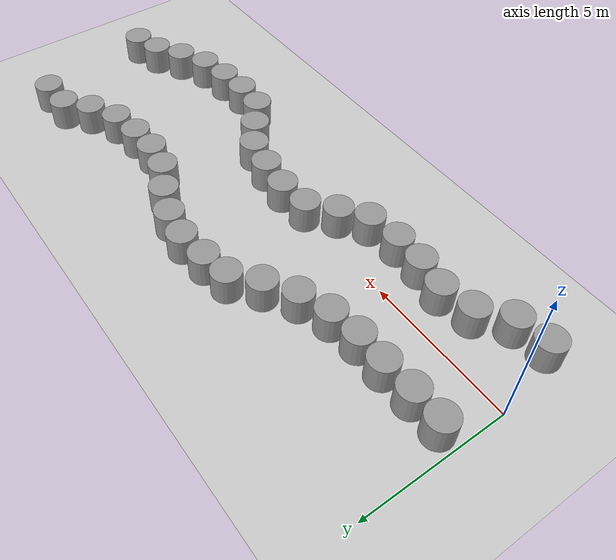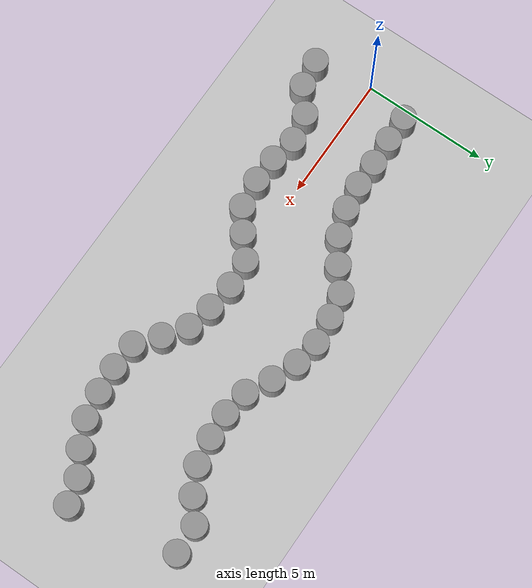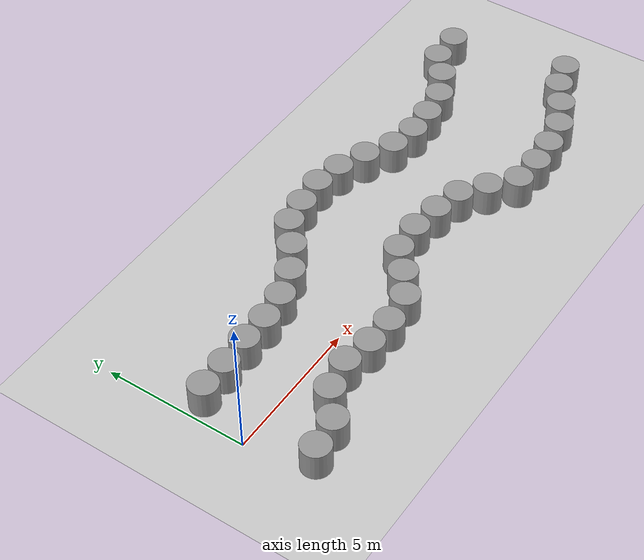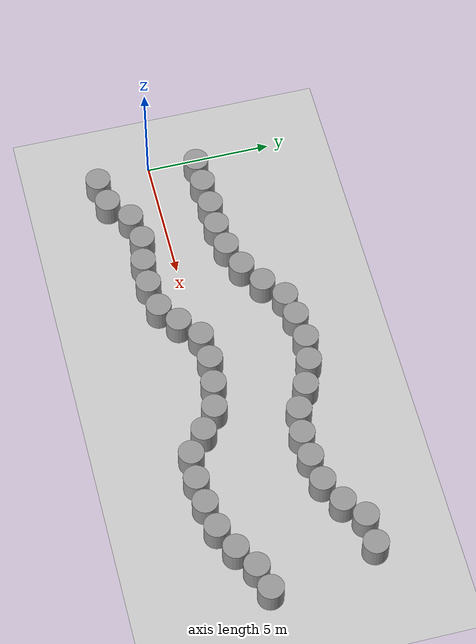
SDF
<sdf version="1.7">
 <world name="default">
  <light name="sun" type="directional">
   <pose>0 0 10 0 -0 0</pose>
   <diffuse>0.8 0.8 0.8 1</diffuse>
   <specular>0.2 0.2 0.2 1</specular>
   <attenuation>
    <range>1000</range>
    <constant>0.9</constant>
    <linear>0.01</linear>
    <quadratic>0.001</quadratic>
   </attenuation>
   <direction>-0.5 0.1 -0.9</direction>
   <spot><inner_angle>0</inner_angle><outer_angle>0</outer_angle><falloff>0</falloff></spot>
  </light>
  <model name="ground_plane">
   <static>1</static>
   <link name="link">
    <collision name="collision">
     <geometry><plane><normal>0 0 1</normal><size>100 100</size></plane></geometry>
     <surface>
      <contact><collide_bitmask>65535</collide_bitmask></contact>
      <friction><ode><mu>100</mu><mu2>50</mu2></ode></friction>
     </surface>
    </collision>
    <visual name="visual">
     <cast_shadows>0</cast_shadows>
     <geometry><plane><normal>0 0 1</normal><size>100 100</size></plane></geometry>
     <material>
      <script><uri>file://media/materials/scripts/gazebo.material</uri><name>Gazebo/Grey</name></script>
     </material>
    </visual>
   </link>
  </model>
  <gravity>0 0 -9.8</gravity>
  <magnetic_field>6e-06 2.3e-05 -4.2e-05</magnetic_field>
  <atmosphere type="adiabatic"/>
  <physics type="ode">
   <max_step_size>0.001</max_step_size>
   <real_time_factor>1</real_time_factor>
   <real_time_update_rate>1000</real_time_update_rate>
  </physics>
  <scene><ambient>0.4 0.4 0.4 1</ambient><background>0.7 0.7 0.7 1</background><shadows>1</shadows></scene>
  <spherical_coordinates>
   <surface_model>EARTH_WGS84</surface_model>
   <latitude_deg>0</latitude_deg>
   <longitude_deg>0</longitude_deg>
   <elevation>0</elevation>
   <heading_deg>0</heading_deg>
  </spherical_coordinates>
  <model name="gasse_zylinder">
   <link name="link_0">
    <inertial>
     <mass>1</mass>
     <inertia><ixx>0.145833</ixx><ixy>0</ixy><ixz>0</ixz><iyy>0.145833</iyy><iyz>0</iyz><izz>0.125</izz></inertia>
    </inertial>
    <pose>-9.35991 0.82655 0 0 -0 0</pose>
    <visual name="visual">
     <geometry><cylinder><radius>0.5</radius><length>1</length></cylinder></geometry>
     <material>
      <lighting>1</lighting>
      <script><uri>file://media/materials/scripts/gazebo.material</uri><name>Gazebo/Grey</name></script>
      <shader type="pixel"/>
     </material>
    </visual>
    <collision name="collision">
     <geometry><cylinder><radius>0.5</radius><length>1</length></cylinder></geometry>
     <surface>
      <friction>
       <ode><mu>1</mu><mu2>1</mu2><fdir1>0 0 0</fdir1><slip1>0</slip1><slip2>0</slip2></ode>
       <torsional>
        <coefficient>1</coefficient>
        <patch_radius>0</patch_radius>
        <surface_radius>0</surface_radius>
        <use_patch_radius>1</use_patch_radius>
        <ode><slip>0</slip></ode>
       </torsional>
      </friction>
      <bounce><restitution_coefficient>0</restitution_coefficient><threshold>1e+06</threshold></bounce>
      <contact>
       <collide_without_contact>0</collide_without_contact>
       <collide_without_contact_bitmask>1</collide_without_contact_bitmask>
       <collide_bitmask>1</collide_bitmask>
       <ode>
        <soft_cfm>0</soft_cfm>
        <soft_erp>0.2</soft_erp>
        <kp>1e+13</kp>
        <kd>1</kd>
        <max_vel>0.01</max_vel>
        <min_depth>0</min_depth>
       </ode>
       <bullet>
        <split_impulse>1</split_impulse>
        <split_impulse_penetration_threshold>-0.01</split_impulse_penetration_threshold>
        <soft_cfm>0</soft_cfm>
        <soft_erp>0.2</soft_erp>
        <kp>1e+13</kp>
        <kd>1</kd>
       </bullet>
      </contact>
     </surface>
    </collision>
   </link>
   <link name="link_1">
    <inertial>
     <mass>1</mass>
     <inertia><ixx>0.145833</ixx><ixy>0</ixy><ixz>0</ixz><iyy>0.145833</iyy><iyz>0</iyz><izz>0.125</izz></inertia>
    </inertial>
    <pose>-8.31745 0.842697 0 0 -0 0</pose>
    <visual name="visual">
     <geometry><cylinder><radius>0.5</radius><length>1</length></cylinder></geometry>
     <material>
      <lighting>1</lighting>
      <script><uri>file://media/materials/scripts/gazebo.material</uri><name>Gazebo/Grey</name></script>
      <shader type="pixel"/>
     </material>
    </visual>
    <collision name="collision">
     <geometry><cylinder><radius>0.5</radius><length>1</length></cylinder></geometry>
     <surface>
      <friction>
       <ode><mu>1</mu><mu2>1</mu2><fdir1>0 0 0</fdir1><slip1>0</slip1><slip2>0</slip2></ode>
       <torsional>
        <coefficient>1</coefficient>
        <patch_radius>0</patch_radius>
        <surface_radius>0</surface_radius>
        <use_patch_radius>1</use_patch_radius>
        <ode><slip>0</slip></ode>
       </torsional>
      </friction>
      <bounce><restitution_coefficient>0</restitution_coefficient><threshold>1e+06</threshold></bounce>
      <contact>
       <collide_without_contact>0</collide_without_contact>
       <collide_without_contact_bitmask>1</collide_without_contact_bitmask>
       <collide_bitmask>1</collide_bitmask>
       <ode>
        <soft_cfm>0</soft_cfm>
        <soft_erp>0.2</soft_erp>
        <kp>1e+13</kp>
        <kd>1</kd>
        <max_vel>0.01</max_vel>
        <min_depth>0</min_depth>
       </ode>
       <bullet>
        <split_impulse>1</split_impulse>
        <split_impulse_penetration_threshold>-0.01</split_impulse_penetration_threshold>
        <soft_cfm>0</soft_cfm>
        <soft_erp>0.2</soft_erp>
        <kp>1e+13</kp>
        <kd>1</kd>
       </bullet>
      </contact>
     </surface>
    </collision>
   </link>
   <link name="link_10">
    <inertial>
     <mass>1</mass>
     <inertia><ixx>0.145833</ixx><ixy>0</ixy><ixz>0</ixz><iyy>0.145833</iyy><iyz>0</iyz><izz>0.125</izz></inertia>
    </inertial>
    <pose>0.729078 2.85746 0 0 -0 0</pose>
    <visual name="visual">
     <geometry><cylinder><radius>0.5</radius><length>1</length></cylinder></geometry>
     <material>
      <lighting>1</lighting>
      <script><uri>file://media/materials/scripts/gazebo.material</uri><name>Gazebo/Grey</name></script>
      <shader type="pixel"/>
     </material>
    </visual>
    <collision name="collision">
     <geometry><cylinder><radius>0.5</radius><length>1</length></cylinder></geometry>
     <surface>
      <friction>
       <ode><mu>1</mu><mu2>1</mu2><fdir1>0 0 0</fdir1><slip1>0</slip1><slip2>0</slip2></ode>
       <torsional>
        <coefficient>1</coefficient>
        <patch_radius>0</patch_radius>
        <surface_radius>0</surface_radius>
        <use_patch_radius>1</use_patch_radius>
        <ode><slip>0</slip></ode>
       </torsional>
      </friction>
      <bounce><restitution_coefficient>0</restitution_coefficient><threshold>1e+06</threshold></bounce>
      <contact>
       <collide_without_contact>0</collide_without_contact>
       <collide_without_contact_bitmask>1</collide_without_contact_bitmask>
       <collide_bitmask>1</collide_bitmask>
       <ode>
        <soft_cfm>0</soft_cfm>
        <soft_erp>0.2</soft_erp>
        <kp>1e+13</kp>
        <kd>1</kd>
        <max_vel>0.01</max_vel>
        <min_depth>0</min_depth>
       </ode>
       <bullet>
        <split_impulse>1</split_impulse>
        <split_impulse_penetration_threshold>-0.01</split_impulse_penetration_threshold>
        <soft_cfm>0</soft_cfm>
        <soft_erp>0.2</soft_erp>
        <kp>1e+13</kp>
        <kd>1</kd>
       </bullet>
      </contact>
     </surface>
    </collision>
   </link>
   <link name="link_11">
    <inertial>
     <mass>1</mass>
     <inertia><ixx>0.145833</ixx><ixy>0</ixy><ixz>0</ixz><iyy>0.145833</iyy><iyz>0</iyz><izz>0.125</izz></inertia>
    </inertial>
    <pose>1.75035 2.46204 0 0 -0 0</pose>
    <visual name="visual">
     <geometry><cylinder><radius>0.5</radius><length>1</length></cylinder></geometry>
     <material>
      <lighting>1</lighting>
      <script><uri>file://media/materials/scripts/gazebo.material</uri><name>Gazebo/Grey</name></script>
      <shader type="pixel"/>
     </material>
    </visual>
    <collision name="collision">
     <geometry><cylinder><radius>0.5</radius><length>1</length></cylinder></geometry>
     <surface>
      <friction>
       <ode><mu>1</mu><mu2>1</mu2><fdir1>0 0 0</fdir1><slip1>0</slip1><slip2>0</slip2></ode>
       <torsional>
        <coefficient>1</coefficient>
        <patch_radius>0</patch_radius>
        <surface_radius>0</surface_radius>
        <use_patch_radius>1</use_patch_radius>
        <ode><slip>0</slip></ode>
       </torsional>
      </friction>
      <bounce><restitution_coefficient>0</restitution_coefficient><threshold>1e+06</threshold></bounce>
      <contact>
       <collide_without_contact>0</collide_without_contact>
       <collide_without_contact_bitmask>1</collide_without_contact_bitmask>
       <collide_bitmask>1</collide_bitmask>
       <ode>
        <soft_cfm>0</soft_cfm>
        <soft_erp>0.2</soft_erp>
        <kp>1e+13</kp>
        <kd>1</kd>
        <max_vel>0.01</max_vel>
        <min_depth>0</min_depth>
       </ode>
       <bullet>
        <split_impulse>1</split_impulse>
        <split_impulse_penetration_threshold>-0.01</split_impulse_penetration_threshold>
        <soft_cfm>0</soft_cfm>
        <soft_erp>0.2</soft_erp>
        <kp>1e+13</kp>
        <kd>1</kd>
       </bullet>
      </contact>
     </surface>
    </collision>
   </link>
   <link name="link_12">
    <inertial>
     <mass>1</mass>
     <inertia><ixx>0.145833</ixx><ixy>0</ixy><ixz>0</ixz><iyy>0.145833</iyy><iyz>0</iyz><izz>0.125</izz></inertia>
    </inertial>
    <pose>-9.37316 -3.22378 0 0 -0 0</pose>
    <visual name="visual">
     <geometry><cylinder><radius>0.5</radius><length>1</length></cylinder></geometry>
     <material>
      <lighting>1</lighting>
      <script><uri>file://media/materials/scripts/gazebo.material</uri><name>Gazebo/Grey</name></script>
      <shader type="pixel"/>
     </material>
    </visual>
    <collision name="collision">
     <geometry><cylinder><radius>0.5</radius><length>1</length></cylinder></geometry>
     <surface>
      <friction>
       <ode><mu>1</mu><mu2>1</mu2><fdir1>0 0 0</fdir1><slip1>0</slip1><slip2>0</slip2></ode>
       <torsional>
        <coefficient>1</coefficient>
        <patch_radius>0</patch_radius>
        <surface_radius>0</surface_radius>
        <use_patch_radius>1</use_patch_radius>
        <ode><slip>0</slip></ode>
       </torsional>
      </friction>
      <bounce><restitution_coefficient>0</restitution_coefficient><threshold>1e+06</threshold></bounce>
      <contact>
       <collide_without_contact>0</collide_without_contact>
       <collide_without_contact_bitmask>1</collide_without_contact_bitmask>
       <collide_bitmask>1</collide_bitmask>
       <ode>
        <soft_cfm>0</soft_cfm>
        <soft_erp>0.2</soft_erp>
        <kp>1e+13</kp>
        <kd>1</kd>
        <max_vel>0.01</max_vel>
        <min_depth>0</min_depth>
       </ode>
       <bullet>
        <split_impulse>1</split_impulse>
        <split_impulse_penetration_threshold>-0.01</split_impulse_penetration_threshold>
        <soft_cfm>0</soft_cfm>
        <soft_erp>0.2</soft_erp>
        <kp>1e+13</kp>
        <kd>1</kd>
       </bullet>
      </contact>
     </surface>
    </collision>
   </link>
   <link name="link_13">
    <inertial>
     <mass>1</mass>
     <inertia><ixx>0.145833</ixx><ixy>0</ixy><ixz>0</ixz><iyy>0.145833</iyy><iyz>0</iyz><izz>0.125</izz></inertia>
    </inertial>
    <pose>-8.28443 -3.06836 0 0 -0 0</pose>
    <visual name="visual">
     <geometry><cylinder><radius>0.5</radius><length>1</length></cylinder></geometry>
     <material>
      <lighting>1</lighting>
      <script><uri>file://media/materials/scripts/gazebo.material</uri><name>Gazebo/Grey</name></script>
      <shader type="pixel"/>
     </material>
    </visual>
    <collision name="collision">
     <geometry><cylinder><radius>0.5</radius><length>1</length></cylinder></geometry>
     <surface>
      <friction>
       <ode><mu>1</mu><mu2>1</mu2><fdir1>0 0 0</fdir1><slip1>0</slip1><slip2>0</slip2></ode>
       <torsional>
        <coefficient>1</coefficient>
        <patch_radius>0</patch_radius>
        <surface_radius>0</surface_radius>
        <use_patch_radius>1</use_patch_radius>
        <ode><slip>0</slip></ode>
       </torsional>
      </friction>
      <bounce><restitution_coefficient>0</restitution_coefficient><threshold>1e+06</threshold></bounce>
      <contact>
       <collide_without_contact>0</collide_without_contact>
       <collide_without_contact_bitmask>1</collide_without_contact_bitmask>
       <collide_bitmask>1</collide_bitmask>
       <ode>
        <soft_cfm>0</soft_cfm>
        <soft_erp>0.2</soft_erp>
        <kp>1e+13</kp>
        <kd>1</kd>
        <max_vel>0.01</max_vel>
        <min_depth>0</min_depth>
       </ode>
       <bullet>
        <split_impulse>1</split_impulse>
        <split_impulse_penetration_threshold>-0.01</split_impulse_penetration_threshold>
        <soft_cfm>0</soft_cfm>
        <soft_erp>0.2</soft_erp>
        <kp>1e+13</kp>
        <kd>1</kd>
       </bullet>
      </contact>
     </surface>
    </collision>
   </link>
   <link name="link_14">
    <inertial>
     <mass>1</mass>
     <inertia><ixx>0.145833</ixx><ixy>0</ixy><ixz>0</ixz><iyy>0.145833</iyy><iyz>0</iyz><izz>0.125</izz></inertia>
    </inertial>
    <pose>-7.3678 -2.33615 0 0 -0 0</pose>
    <visual name="visual">
     <geometry><cylinder><radius>0.5</radius><length>1</length></cylinder></geometry>
     <material>
      <lighting>1</lighting>
      <script><uri>file://media/materials/scripts/gazebo.material</uri><name>Gazebo/Grey</name></script>
      <shader type="pixel"/>
     </material>
    </visual>
    <collision name="collision">
     <geometry><cylinder><radius>0.5</radius><length>1</length></cylinder></geometry>
     <surface>
      <friction>
       <ode><mu>1</mu><mu2>1</mu2><fdir1>0 0 0</fdir1><slip1>0</slip1><slip2>0</slip2></ode>
       <torsional>
        <coefficient>1</coefficient>
        <patch_radius>0</patch_radius>
        <surface_radius>0</surface_radius>
        <use_patch_radius>1</use_patch_radius>
        <ode><slip>0</slip></ode>
       </torsional>
      </friction>
      <bounce><restitution_coefficient>0</restitution_coefficient><threshold>1e+06</threshold></bounce>
      <contact>
       <collide_without_contact>0</collide_without_contact>
       <collide_without_contact_bitmask>1</collide_without_contact_bitmask>
       <collide_bitmask>1</collide_bitmask>
       <ode>
        <soft_cfm>0</soft_cfm>
        <soft_erp>0.2</soft_erp>
        <kp>1e+13</kp>
        <kd>1</kd>
        <max_vel>0.01</max_vel>
        <min_depth>0</min_depth>
       </ode>
       <bullet>
        <split_impulse>1</split_impulse>
        <split_impulse_penetration_threshold>-0.01</split_impulse_penetration_threshold>
        <soft_cfm>0</soft_cfm>
        <soft_erp>0.2</soft_erp>
        <kp>1e+13</kp>
        <kd>1</kd>
       </bullet>
      </contact>
     </surface>
    </collision>
   </link>
   <link name="link_15">
    <inertial>
     <mass>1</mass>
     <inertia><ixx>0.145833</ixx><ixy>0</ixy><ixz>0</ixz><iyy>0.145833</iyy><iyz>0</iyz><izz>0.125</izz></inertia>
    </inertial>
    <pose>-6.25209 -2.12005 0 0 -0 0</pose>
    <visual name="visual">
     <geometry><cylinder><radius>0.5</radius><length>1</length></cylinder></geometry>
     <material>
      <lighting>1</lighting>
      <script><uri>file://media/materials/scripts/gazebo.material</uri><name>Gazebo/Grey</name></script>
      <shader type="pixel"/>
     </material>
    </visual>
    <collision name="collision">
     <geometry><cylinder><radius>0.5</radius><length>1</length></cylinder></geometry>
     <surface>
      <friction>
       <ode><mu>1</mu><mu2>1</mu2><fdir1>0 0 0</fdir1><slip1>0</slip1><slip2>0</slip2></ode>
       <torsional>
        <coefficient>1</coefficient>
        <patch_radius>0</patch_radius>
        <surface_radius>0</surface_radius>
        <use_patch_radius>1</use_patch_radius>
        <ode><slip>0</slip></ode>
       </torsional>
      </friction>
      <bounce><restitution_coefficient>0</restitution_coefficient><threshold>1e+06</threshold></bounce>
      <contact>
       <collide_without_contact>0</collide_without_contact>
       <collide_without_contact_bitmask>1</collide_without_contact_bitmask>
       <collide_bitmask>1</collide_bitmask>
       <ode>
        <soft_cfm>0</soft_cfm>
        <soft_erp>0.2</soft_erp>
        <kp>1e+13</kp>
        <kd>1</kd>
        <max_vel>0.01</max_vel>
        <min_depth>0</min_depth>
       </ode>
       <bullet>
        <split_impulse>1</split_impulse>
        <split_impulse_penetration_threshold>-0.01</split_impulse_penetration_threshold>
        <soft_cfm>0</soft_cfm>
        <soft_erp>0.2</soft_erp>
        <kp>1e+13</kp>
        <kd>1</kd>
       </bullet>
      </contact>
     </surface>
    </collision>
   </link>
   <link name="link_16">
    <inertial>
     <mass>1</mass>
     <inertia><ixx>0.145833</ixx><ixy>0</ixy><ixz>0</ixz><iyy>0.145833</iyy><iyz>0</iyz><izz>0.125</izz></inertia>
    </inertial>
    <pose>-5.21227 -2.31195 0 0 -0 0</pose>
    <visual name="visual">
     <geometry><cylinder><radius>0.5</radius><length>1</length></cylinder></geometry>
     <material>
      <lighting>1</lighting>
      <script><uri>file://media/materials/scripts/gazebo.material</uri><name>Gazebo/Grey</name></script>
      <shader type="pixel"/>
     </material>
    </visual>
    <collision name="collision">
     <geometry><cylinder><radius>0.5</radius><length>1</length></cylinder></geometry>
     <surface>
      <friction>
       <ode><mu>1</mu><mu2>1</mu2><fdir1>0 0 0</fdir1><slip1>0</slip1><slip2>0</slip2></ode>
       <torsional>
        <coefficient>1</coefficient>
        <patch_radius>0</patch_radius>
        <surface_radius>0</surface_radius>
        <use_patch_radius>1</use_patch_radius>
        <ode><slip>0</slip></ode>
       </torsional>
      </friction>
      <bounce><restitution_coefficient>0</restitution_coefficient><threshold>1e+06</threshold></bounce>
      <contact>
       <collide_without_contact>0</collide_without_contact>
       <collide_without_contact_bitmask>1</collide_without_contact_bitmask>
       <collide_bitmask>1</collide_bitmask>
       <ode>
        <soft_cfm>0</soft_cfm>
        <soft_erp>0.2</soft_erp>
        <kp>1e+13</kp>
        <kd>1</kd>
        <max_vel>0.01</max_vel>
        <min_depth>0</min_depth>
       </ode>
       <bullet>
        <split_impulse>1</split_impulse>
        <split_impulse_penetration_threshold>-0.01</split_impulse_penetration_threshold>
        <soft_cfm>0</soft_cfm>
        <soft_erp>0.2</soft_erp>
        <kp>1e+13</kp>
        <kd>1</kd>
       </bullet>
      </contact>
     </surface>
    </collision>
   </link>
   <link name="link_17">
    <inertial>
     <mass>1</mass>
     <inertia><ixx>0.145833</ixx><ixy>0</ixy><ixz>0</ixz><iyy>0.145833</iyy><iyz>0</iyz><izz>0.125</izz></inertia>
    </inertial>
    <pose>-4.16804 -2.34618 0 0 -0 0</pose>
    <visual name="visual">
     <geometry><cylinder><radius>0.5</radius><length>1</length></cylinder></geometry>
     <material>
      <lighting>1</lighting>
      <script><uri>file://media/materials/scripts/gazebo.material</uri><name>Gazebo/Grey</name></script>
      <shader type="pixel"/>
     </material>
    </visual>
    <collision name="collision">
     <geometry><cylinder><radius>0.5</radius><length>1</length></cylinder></geometry>
     <surface>
      <friction>
       <ode><mu>1</mu><mu2>1</mu2><fdir1>0 0 0</fdir1><slip1>0</slip1><slip2>0</slip2></ode>
       <torsional>
        <coefficient>1</coefficient>
        <patch_radius>0</patch_radius>
        <surface_radius>0</surface_radius>
        <use_patch_radius>1</use_patch_radius>
        <ode><slip>0</slip></ode>
       </torsional>
      </friction>
      <bounce><restitution_coefficient>0</restitution_coefficient><threshold>1e+06</threshold></bounce>
      <contact>
       <collide_without_contact>0</collide_without_contact>
       <collide_without_contact_bitmask>1</collide_without_contact_bitmask>
       <collide_bitmask>1</collide_bitmask>
       <ode>
        <soft_cfm>0</soft_cfm>
        <soft_erp>0.2</soft_erp>
        <kp>1e+13</kp>
        <kd>1</kd>
        <max_vel>0.01</max_vel>
        <min_depth>0</min_depth>
       </ode>
       <bullet>
        <split_impulse>1</split_impulse>
        <split_impulse_penetration_threshold>-0.01</split_impulse_penetration_threshold>
        <soft_cfm>0</soft_cfm>
        <soft_erp>0.2</soft_erp>
        <kp>1e+13</kp>
        <kd>1</kd>
       </bullet>
      </contact>
     </surface>
    </collision>
   </link>
   <link name="link_18">
    <inertial>
     <mass>1</mass>
     <inertia><ixx>0.145833</ixx><ixy>0</ixy><ixz>0</ixz><iyy>0.145833</iyy><iyz>0</iyz><izz>0.125</izz></inertia>
    </inertial>
    <pose>-3.02576 -2.19398 0 0 -0 0</pose>
    <visual name="visual">
     <geometry><cylinder><radius>0.5</radius><length>1</length></cylinder></geometry>
     <material>
      <lighting>1</lighting>
      <script><uri>file://media/materials/scripts/gazebo.material</uri><name>Gazebo/Grey</name></script>
      <shader type="pixel"/>
     </material>
    </visual>
    <collision name="collision">
     <geometry><cylinder><radius>0.5</radius><length>1</length></cylinder></geometry>
     <surface>
      <friction>
       <ode><mu>1</mu><mu2>1</mu2><fdir1>0 0 0</fdir1><slip1>0</slip1><slip2>0</slip2></ode>
       <torsional>
        <coefficient>1</coefficient>
        <patch_radius>0</patch_radius>
        <surface_radius>0</surface_radius>
        <use_patch_radius>1</use_patch_radius>
        <ode><slip>0</slip></ode>
       </torsional>
      </friction>
      <bounce><restitution_coefficient>0</restitution_coefficient><threshold>1e+06</threshold></bounce>
      <contact>
       <collide_without_contact>0</collide_without_contact>
       <collide_without_contact_bitmask>1</collide_without_contact_bitmask>
       <collide_bitmask>1</collide_bitmask>
       <ode>
        <soft_cfm>0</soft_cfm>
        <soft_erp>0.2</soft_erp>
        <kp>1e+13</kp>
        <kd>1</kd>
        <max_vel>0.01</max_vel>
        <min_depth>0</min_depth>
       </ode>
       <bullet>
        <split_impulse>1</split_impulse>
        <split_impulse_penetration_threshold>-0.01</split_impulse_penetration_threshold>
        <soft_cfm>0</soft_cfm>
        <soft_erp>0.2</soft_erp>
        <kp>1e+13</kp>
        <kd>1</kd>
       </bullet>
      </contact>
     </surface>
    </collision>
   </link>
   <link name="link_19">
    <inertial>
     <mass>1</mass>
     <inertia><ixx>0.145833</ixx><ixy>0</ixy><ixz>0</ixz><iyy>0.145833</iyy><iyz>0</iyz><izz>0.125</izz></inertia>
    </inertial>
    <pose>-2.19618 -1.59246 0 0 -0 0</pose>
    <visual name="visual">
     <geometry><cylinder><radius>0.5</radius><length>1</length></cylinder></geometry>
     <material>
      <lighting>1</lighting>
      <script><uri>file://media/materials/scripts/gazebo.material</uri><name>Gazebo/Grey</name></script>
      <shader type="pixel"/>
     </material>
    </visual>
    <collision name="collision">
     <geometry><cylinder><radius>0.5</radius><length>1</length></cylinder></geometry>
     <surface>
      <friction>
       <ode><mu>1</mu><mu2>1</mu2><fdir1>0 0 0</fdir1><slip1>0</slip1><slip2>0</slip2></ode>
       <torsional>
        <coefficient>1</coefficient>
        <patch_radius>0</patch_radius>
        <surface_radius>0</surface_radius>
        <use_patch_radius>1</use_patch_radius>
        <ode><slip>0</slip></ode>
       </torsional>
      </friction>
      <bounce><restitution_coefficient>0</restitution_coefficient><threshold>1e+06</threshold></bounce>
      <contact>
       <collide_without_contact>0</collide_without_contact>
       <collide_without_contact_bitmask>1</collide_without_contact_bitmask>
       <collide_bitmask>1</collide_bitmask>
       <ode>
        <soft_cfm>0</soft_cfm>
        <soft_erp>0.2</soft_erp>
        <kp>1e+13</kp>
        <kd>1</kd>
        <max_vel>0.01</max_vel>
        <min_depth>0</min_depth>
       </ode>
       <bullet>
        <split_impulse>1</split_impulse>
        <split_impulse_penetration_threshold>-0.01</split_impulse_penetration_threshold>
        <soft_cfm>0</soft_cfm>
        <soft_erp>0.2</soft_erp>
        <kp>1e+13</kp>
        <kd>1</kd>
       </bullet>
      </contact>
     </surface>
    </collision>
   </link>
   <link name="link_2">
    <inertial>
     <mass>1</mass>
     <inertia><ixx>0.145833</ixx><ixy>0</ixy><ixz>0</ixz><iyy>0.145833</iyy><iyz>0</iyz><izz>0.125</izz></inertia>
    </inertial>
    <pose>-7.22171 0.898803 0 0 -0 0</pose>
    <visual name="visual">
     <geometry><cylinder><radius>0.5</radius><length>1</length></cylinder></geometry>
     <material>
      <lighting>1</lighting>
      <script><uri>file://media/materials/scripts/gazebo.material</uri><name>Gazebo/Grey</name></script>
      <shader type="pixel"/>
     </material>
    </visual>
    <collision name="collision">
     <geometry><cylinder><radius>0.5</radius><length>1</length></cylinder></geometry>
     <surface>
      <friction>
       <ode><mu>1</mu><mu2>1</mu2><fdir1>0 0 0</fdir1><slip1>0</slip1><slip2>0</slip2></ode>
       <torsional>
        <coefficient>1</coefficient>
        <patch_radius>0</patch_radius>
        <surface_radius>0</surface_radius>
        <use_patch_radius>1</use_patch_radius>
        <ode><slip>0</slip></ode>
       </torsional>
      </friction>
      <bounce><restitution_coefficient>0</restitution_coefficient><threshold>1e+06</threshold></bounce>
      <contact>
       <collide_without_contact>0</collide_without_contact>
       <collide_without_contact_bitmask>1</collide_without_contact_bitmask>
       <collide_bitmask>1</collide_bitmask>
       <ode>
        <soft_cfm>0</soft_cfm>
        <soft_erp>0.2</soft_erp>
        <kp>1e+13</kp>
        <kd>1</kd>
        <max_vel>0.01</max_vel>
        <min_depth>0</min_depth>
       </ode>
       <bullet>
        <split_impulse>1</split_impulse>
        <split_impulse_penetration_threshold>-0.01</split_impulse_penetration_threshold>
        <soft_cfm>0</soft_cfm>
        <soft_erp>0.2</soft_erp>
        <kp>1e+13</kp>
        <kd>1</kd>
       </bullet>
      </contact>
     </surface>
    </collision>
   </link>
   <link name="link_20">
    <inertial>
     <mass>1</mass>
     <inertia><ixx>0.145833</ixx><ixy>0</ixy><ixz>0</ixz><iyy>0.145833</iyy><iyz>0</iyz><izz>0.125</izz></inertia>
    </inertial>
    <pose>-1.37016 -0.900286 0 0 -0 0</pose>
    <visual name="visual">
     <geometry><cylinder><radius>0.5</radius><length>1</length></cylinder></geometry>
     <material>
      <lighting>1</lighting>
      <script><uri>file://media/materials/scripts/gazebo.material</uri><name>Gazebo/Grey</name></script>
      <shader type="pixel"/>
     </material>
    </visual>
    <collision name="collision">
     <geometry><cylinder><radius>0.5</radius><length>1</length></cylinder></geometry>
     <surface>
      <friction>
       <ode><mu>1</mu><mu2>1</mu2><fdir1>0 0 0</fdir1><slip1>0</slip1><slip2>0</slip2></ode>
       <torsional>
        <coefficient>1</coefficient>
        <patch_radius>0</patch_radius>
        <surface_radius>0</surface_radius>
        <use_patch_radius>1</use_patch_radius>
        <ode><slip>0</slip></ode>
       </torsional>
      </friction>
      <bounce><restitution_coefficient>0</restitution_coefficient><threshold>1e+06</threshold></bounce>
      <contact>
       <collide_without_contact>0</collide_without_contact>
       <collide_without_contact_bitmask>1</collide_without_contact_bitmask>
       <collide_bitmask>1</collide_bitmask>
       <ode>
        <soft_cfm>0</soft_cfm>
        <soft_erp>0.2</soft_erp>
        <kp>1e+13</kp>
        <kd>1</kd>
        <max_vel>0.01</max_vel>
        <min_depth>0</min_depth>
       </ode>
       <bullet>
        <split_impulse>1</split_impulse>
        <split_impulse_penetration_threshold>-0.01</split_impulse_penetration_threshold>
        <soft_cfm>0</soft_cfm>
        <soft_erp>0.2</soft_erp>
        <kp>1e+13</kp>
        <kd>1</kd>
       </bullet>
      </contact>
     </surface>
    </collision>
   </link>
   <link name="link_21">
    <inertial>
     <mass>1</mass>
     <inertia><ixx>0.145833</ixx><ixy>0</ixy><ixz>0</ixz><iyy>0.145833</iyy><iyz>0</iyz><izz>0.125</izz></inertia>
    </inertial>
    <pose>-0.270384 -0.811496 0 0 -0 0</pose>
    <visual name="visual">
     <geometry><cylinder><radius>0.5</radius><length>1</length></cylinder></geometry>
     <material>
      <lighting>1</lighting>
      <script><uri>file://media/materials/scripts/gazebo.material</uri><name>Gazebo/Grey</name></script>
      <shader type="pixel"/>
     </material>
    </visual>
    <collision name="collision">
     <geometry><cylinder><radius>0.5</radius><length>1</length></cylinder></geometry>
     <surface>
      <friction>
       <ode><mu>1</mu><mu2>1</mu2><fdir1>0 0 0</fdir1><slip1>0</slip1><slip2>0</slip2></ode>
       <torsional>
        <coefficient>1</coefficient>
        <patch_radius>0</patch_radius>
        <surface_radius>0</surface_radius>
        <use_patch_radius>1</use_patch_radius>
        <ode><slip>0</slip></ode>
       </torsional>
      </friction>
      <bounce><restitution_coefficient>0</restitution_coefficient><threshold>1e+06</threshold></bounce>
      <contact>
       <collide_without_contact>0</collide_without_contact>
       <collide_without_contact_bitmask>1</collide_without_contact_bitmask>
       <collide_bitmask>1</collide_bitmask>
       <ode>
        <soft_cfm>0</soft_cfm>
        <soft_erp>0.2</soft_erp>
        <kp>1e+13</kp>
        <kd>1</kd>
        <max_vel>0.01</max_vel>
        <min_depth>0</min_depth>
       </ode>
       <bullet>
        <split_impulse>1</split_impulse>
        <split_impulse_penetration_threshold>-0.01</split_impulse_penetration_threshold>
        <soft_cfm>0</soft_cfm>
        <soft_erp>0.2</soft_erp>
        <kp>1e+13</kp>
        <kd>1</kd>
       </bullet>
      </contact>
     </surface>
    </collision>
   </link>
   <link name="link_22">
    <inertial>
     <mass>1</mass>
     <inertia><ixx>0.145833</ixx><ixy>0</ixy><ixz>0</ixz><iyy>0.145833</iyy><iyz>0</iyz><izz>0.125</izz></inertia>
    </inertial>
    <pose>0.829348 -0.940978 0 0 -0 0</pose>
    <visual name="visual">
     <geometry><cylinder><radius>0.5</radius><length>1</length></cylinder></geometry>
     <material>
      <lighting>1</lighting>
      <script><uri>file://media/materials/scripts/gazebo.material</uri><name>Gazebo/Grey</name></script>
      <shader type="pixel"/>
     </material>
    </visual>
    <collision name="collision">
     <geometry><cylinder><radius>0.5</radius><length>1</length></cylinder></geometry>
     <surface>
      <friction>
       <ode><mu>1</mu><mu2>1</mu2><fdir1>0 0 0</fdir1><slip1>0</slip1><slip2>0</slip2></ode>
       <torsional>
        <coefficient>1</coefficient>
        <patch_radius>0</patch_radius>
        <surface_radius>0</surface_radius>
        <use_patch_radius>1</use_patch_radius>
        <ode><slip>0</slip></ode>
       </torsional>
      </friction>
      <bounce><restitution_coefficient>0</restitution_coefficient><threshold>1e+06</threshold></bounce>
      <contact>
       <collide_without_contact>0</collide_without_contact>
       <collide_without_contact_bitmask>1</collide_without_contact_bitmask>
       <collide_bitmask>1</collide_bitmask>
       <ode>
        <soft_cfm>0</soft_cfm>
        <soft_erp>0.2</soft_erp>
        <kp>1e+13</kp>
        <kd>1</kd>
        <max_vel>0.01</max_vel>
        <min_depth>0</min_depth>
       </ode>
       <bullet>
        <split_impulse>1</split_impulse>
        <split_impulse_penetration_threshold>-0.01</split_impulse_penetration_threshold>
        <soft_cfm>0</soft_cfm>
        <soft_erp>0.2</soft_erp>
        <kp>1e+13</kp>
        <kd>1</kd>
       </bullet>
      </contact>
     </surface>
    </collision>
   </link>
   <link name="link_23">
    <inertial>
     <mass>1</mass>
     <inertia><ixx>0.145833</ixx><ixy>0</ixy><ixz>0</ixz><iyy>0.145833</iyy><iyz>0</iyz><izz>0.125</izz></inertia>
    </inertial>
    <pose>1.86699 -1.16181 0 0 -0 0</pose>
    <visual name="visual">
     <geometry><cylinder><radius>0.5</radius><length>1</length></cylinder></geometry>
     <material>
      <lighting>1</lighting>
      <script><uri>file://media/materials/scripts/gazebo.material</uri><name>Gazebo/Grey</name></script>
      <shader type="pixel"/>
     </material>
    </visual>
    <collision name="collision">
     <geometry><cylinder><radius>0.5</radius><length>1</length></cylinder></geometry>
     <surface>
      <friction>
       <ode><mu>1</mu><mu2>1</mu2><fdir1>0 0 0</fdir1><slip1>0</slip1><slip2>0</slip2></ode>
       <torsional>
        <coefficient>1</coefficient>
        <patch_radius>0</patch_radius>
        <surface_radius>0</surface_radius>
        <use_patch_radius>1</use_patch_radius>
        <ode><slip>0</slip></ode>
       </torsional>
      </friction>
      <bounce><restitution_coefficient>0</restitution_coefficient><threshold>1e+06</threshold></bounce>
      <contact>
       <collide_without_contact>0</collide_without_contact>
       <collide_without_contact_bitmask>1</collide_without_contact_bitmask>
       <collide_bitmask>1</collide_bitmask>
       <ode>
        <soft_cfm>0</soft_cfm>
        <soft_erp>0.2</soft_erp>
        <kp>1e+13</kp>
        <kd>1</kd>
        <max_vel>0.01</max_vel>
        <min_depth>0</min_depth>
       </ode>
       <bullet>
        <split_impulse>1</split_impulse>
        <split_impulse_penetration_threshold>-0.01</split_impulse_penetration_threshold>
        <soft_cfm>0</soft_cfm>
        <soft_erp>0.2</soft_erp>
        <kp>1e+13</kp>
        <kd>1</kd>
       </bullet>
      </contact>
     </surface>
    </collision>
   </link>
   <link name="link_24">
    <inertial>
     <mass>1</mass>
     <inertia><ixx>0.145833</ixx><ixy>0</ixy><ixz>0</ixz><iyy>0.145833</iyy><iyz>0</iyz><izz>0.125</izz></inertia>
    </inertial>
    <pose>2.71438 1.9468 0 0 -0 0</pose>
    <visual name="visual">
     <geometry><cylinder><radius>0.5</radius><length>1</length></cylinder></geometry>
     <material>
      <lighting>1</lighting>
      <script><uri>file://media/materials/scripts/gazebo.material</uri><name>Gazebo/Grey</name></script>
      <shader type="pixel"/>
     </material>
    </visual>
    <collision name="collision">
     <geometry><cylinder><radius>0.5</radius><length>1</length></cylinder></geometry>
     <surface>
      <friction>
       <ode><mu>1</mu><mu2>1</mu2><fdir1>0 0 0</fdir1><slip1>0</slip1><slip2>0</slip2></ode>
       <torsional>
        <coefficient>1</coefficient>
        <patch_radius>0</patch_radius>
        <surface_radius>0</surface_radius>
        <use_patch_radius>1</use_patch_radius>
        <ode><slip>0</slip></ode>
       </torsional>
      </friction>
      <bounce><restitution_coefficient>0</restitution_coefficient><threshold>1e+06</threshold></bounce>
      <contact>
       <collide_without_contact>0</collide_without_contact>
       <collide_without_contact_bitmask>1</collide_without_contact_bitmask>
       <collide_bitmask>1</collide_bitmask>
       <ode>
        <soft_cfm>0</soft_cfm>
        <soft_erp>0.2</soft_erp>
        <kp>1e+13</kp>
        <kd>1</kd>
        <max_vel>0.01</max_vel>
        <min_depth>0</min_depth>
       </ode>
       <bullet>
        <split_impulse>1</split_impulse>
        <split_impulse_penetration_threshold>-0.01</split_impulse_penetration_threshold>
        <soft_cfm>0</soft_cfm>
        <soft_erp>0.2</soft_erp>
        <kp>1e+13</kp>
        <kd>1</kd>
       </bullet>
      </contact>
     </surface>
    </collision>
   </link>
   <link name="link_25">
    <inertial>
     <mass>1</mass>
     <inertia><ixx>0.145833</ixx><ixy>0</ixy><ixz>0</ixz><iyy>0.145833</iyy><iyz>0</iyz><izz>0.125</izz></inertia>
    </inertial>
    <pose>3.73874 1.79215 0 0 -0 0</pose>
    <visual name="visual">
     <geometry><cylinder><radius>0.5</radius><length>1</length></cylinder></geometry>
     <material>
      <lighting>1</lighting>
      <script><uri>file://media/materials/scripts/gazebo.material</uri><name>Gazebo/Grey</name></script>
      <shader type="pixel"/>
     </material>
    </visual>
    <collision name="collision">
     <geometry><cylinder><radius>0.5</radius><length>1</length></cylinder></geometry>
     <surface>
      <friction>
       <ode><mu>1</mu><mu2>1</mu2><fdir1>0 0 0</fdir1><slip1>0</slip1><slip2>0</slip2></ode>
       <torsional>
        <coefficient>1</coefficient>
        <patch_radius>0</patch_radius>
        <surface_radius>0</surface_radius>
        <use_patch_radius>1</use_patch_radius>
        <ode><slip>0</slip></ode>
       </torsional>
      </friction>
      <bounce><restitution_coefficient>0</restitution_coefficient><threshold>1e+06</threshold></bounce>
      <contact>
       <collide_without_contact>0</collide_without_contact>
       <collide_without_contact_bitmask>1</collide_without_contact_bitmask>
       <collide_bitmask>1</collide_bitmask>
       <ode>
        <soft_cfm>0</soft_cfm>
        <soft_erp>0.2</soft_erp>
        <kp>1e+13</kp>
        <kd>1</kd>
        <max_vel>0.01</max_vel>
        <min_depth>0</min_depth>
       </ode>
       <bullet>
        <split_impulse>1</split_impulse>
        <split_impulse_penetration_threshold>-0.01</split_impulse_penetration_threshold>
        <soft_cfm>0</soft_cfm>
        <soft_erp>0.2</soft_erp>
        <kp>1e+13</kp>
        <kd>1</kd>
       </bullet>
      </contact>
     </surface>
    </collision>
   </link>
   <link name="link_26">
    <inertial>
     <mass>1</mass>
     <inertia><ixx>0.145833</ixx><ixy>0</ixy><ixz>0</ixz><iyy>0.145833</iyy><iyz>0</iyz><izz>0.125</izz></inertia>
    </inertial>
    <pose>4.76046 1.84958 0 0 -0 0</pose>
    <visual name="visual">
     <geometry><cylinder><radius>0.5</radius><length>1</length></cylinder></geometry>
     <material>
      <lighting>1</lighting>
      <script><uri>file://media/materials/scripts/gazebo.material</uri><name>Gazebo/Grey</name></script>
      <shader type="pixel"/>
     </material>
    </visual>
    <collision name="collision">
     <geometry><cylinder><radius>0.5</radius><length>1</length></cylinder></geometry>
     <surface>
      <friction>
       <ode><mu>1</mu><mu2>1</mu2><fdir1>0 0 0</fdir1><slip1>0</slip1><slip2>0</slip2></ode>
       <torsional>
        <coefficient>1</coefficient>
        <patch_radius>0</patch_radius>
        <surface_radius>0</surface_radius>
        <use_patch_radius>1</use_patch_radius>
        <ode><slip>0</slip></ode>
       </torsional>
      </friction>
      <bounce><restitution_coefficient>0</restitution_coefficient><threshold>1e+06</threshold></bounce>
      <contact>
       <collide_without_contact>0</collide_without_contact>
       <collide_without_contact_bitmask>1</collide_without_contact_bitmask>
       <collide_bitmask>1</collide_bitmask>
       <ode>
        <soft_cfm>0</soft_cfm>
        <soft_erp>0.2</soft_erp>
        <kp>1e+13</kp>
        <kd>1</kd>
        <max_vel>0.01</max_vel>
        <min_depth>0</min_depth>
       </ode>
       <bullet>
        <split_impulse>1</split_impulse>
        <split_impulse_penetration_threshold>-0.01</split_impulse_penetration_threshold>
        <soft_cfm>0</soft_cfm>
        <soft_erp>0.2</soft_erp>
        <kp>1e+13</kp>
        <kd>1</kd>
       </bullet>
      </contact>
     </surface>
    </collision>
   </link>
   <link name="link_27">
    <inertial>
     <mass>1</mass>
     <inertia><ixx>0.145833</ixx><ixy>0</ixy><ixz>0</ixz><iyy>0.145833</iyy><iyz>0</iyz><izz>0.125</izz></inertia>
    </inertial>
    <pose>5.84036 2.02666 0 0 -0 0</pose>
    <visual name="visual">
     <geometry><cylinder><radius>0.5</radius><length>1</length></cylinder></geometry>
     <material>
      <lighting>1</lighting>
      <script><uri>file://media/materials/scripts/gazebo.material</uri><name>Gazebo/Grey</name></script>
      <shader type="pixel"/>
     </material>
    </visual>
    <collision name="collision">
     <geometry><cylinder><radius>0.5</radius><length>1</length></cylinder></geometry>
     <surface>
      <friction>
       <ode><mu>1</mu><mu2>1</mu2><fdir1>0 0 0</fdir1><slip1>0</slip1><slip2>0</slip2></ode>
       <torsional>
        <coefficient>1</coefficient>
        <patch_radius>0</patch_radius>
        <surface_radius>0</surface_radius>
        <use_patch_radius>1</use_patch_radius>
        <ode><slip>0</slip></ode>
       </torsional>
      </friction>
      <bounce><restitution_coefficient>0</restitution_coefficient><threshold>1e+06</threshold></bounce>
      <contact>
       <collide_without_contact>0</collide_without_contact>
       <collide_without_contact_bitmask>1</collide_without_contact_bitmask>
       <collide_bitmask>1</collide_bitmask>
       <ode>
        <soft_cfm>0</soft_cfm>
        <soft_erp>0.2</soft_erp>
        <kp>1e+13</kp>
        <kd>1</kd>
        <max_vel>0.01</max_vel>
        <min_depth>0</min_depth>
       </ode>
       <bullet>
        <split_impulse>1</split_impulse>
        <split_impulse_penetration_threshold>-0.01</split_impulse_penetration_threshold>
        <soft_cfm>0</soft_cfm>
        <soft_erp>0.2</soft_erp>
        <kp>1e+13</kp>
        <kd>1</kd>
       </bullet>
      </contact>
     </surface>
    </collision>
   </link>
   <link name="link_28">
    <inertial>
     <mass>1</mass>
     <inertia><ixx>0.145833</ixx><ixy>0</ixy><ixz>0</ixz><iyy>0.145833</iyy><iyz>0</iyz><izz>0.125</izz></inertia>
    </inertial>
    <pose>2.72293 -1.78441 0 0 -0 0</pose>
    <visual name="visual">
     <geometry><cylinder><radius>0.5</radius><length>1</length></cylinder></geometry>
     <material>
      <lighting>1</lighting>
      <script><uri>file://media/materials/scripts/gazebo.material</uri><name>Gazebo/Grey</name></script>
      <shader type="pixel"/>
     </material>
    </visual>
    <collision name="collision">
     <geometry><cylinder><radius>0.5</radius><length>1</length></cylinder></geometry>
     <surface>
      <friction>
       <ode><mu>1</mu><mu2>1</mu2><fdir1>0 0 0</fdir1><slip1>0</slip1><slip2>0</slip2></ode>
       <torsional>
        <coefficient>1</coefficient>
        <patch_radius>0</patch_radius>
        <surface_radius>0</surface_radius>
        <use_patch_radius>1</use_patch_radius>
        <ode><slip>0</slip></ode>
       </torsional>
      </friction>
      <bounce><restitution_coefficient>0</restitution_coefficient><threshold>1e+06</threshold></bounce>
      <contact>
       <collide_without_contact>0</collide_without_contact>
       <collide_without_contact_bitmask>1</collide_without_contact_bitmask>
       <collide_bitmask>1</collide_bitmask>
       <ode>
        <soft_cfm>0</soft_cfm>
        <soft_erp>0.2</soft_erp>
        <kp>1e+13</kp>
        <kd>1</kd>
        <max_vel>0.01</max_vel>
        <min_depth>0</min_depth>
       </ode>
       <bullet>
        <split_impulse>1</split_impulse>
        <split_impulse_penetration_threshold>-0.01</split_impulse_penetration_threshold>
        <soft_cfm>0</soft_cfm>
        <soft_erp>0.2</soft_erp>
        <kp>1e+13</kp>
        <kd>1</kd>
       </bullet>
      </contact>
     </surface>
    </collision>
   </link>
   <link name="link_29">
    <inertial>
     <mass>1</mass>
     <inertia><ixx>0.145833</ixx><ixy>0</ixy><ixz>0</ixz><iyy>0.145833</iyy><iyz>0</iyz><izz>0.125</izz></inertia>
    </inertial>
    <pose>3.5838 -2.47343 0 0 -0 0</pose>
    <visual name="visual">
     <geometry><cylinder><radius>0.5</radius><length>1</length></cylinder></geometry>
     <material>
      <lighting>1</lighting>
      <script><uri>file://media/materials/scripts/gazebo.material</uri><name>Gazebo/Grey</name></script>
      <shader type="pixel"/>
     </material>
    </visual>
    <collision name="collision">
     <geometry><cylinder><radius>0.5</radius><length>1</length></cylinder></geometry>
     <surface>
      <friction>
       <ode><mu>1</mu><mu2>1</mu2><fdir1>0 0 0</fdir1><slip1>0</slip1><slip2>0</slip2></ode>
       <torsional>
        <coefficient>1</coefficient>
        <patch_radius>0</patch_radius>
        <surface_radius>0</surface_radius>
        <use_patch_radius>1</use_patch_radius>
        <ode><slip>0</slip></ode>
       </torsional>
      </friction>
      <bounce><restitution_coefficient>0</restitution_coefficient><threshold>1e+06</threshold></bounce>
      <contact>
       <collide_without_contact>0</collide_without_contact>
       <collide_without_contact_bitmask>1</collide_without_contact_bitmask>
       <collide_bitmask>1</collide_bitmask>
       <ode>
        <soft_cfm>0</soft_cfm>
        <soft_erp>0.2</soft_erp>
        <kp>1e+13</kp>
        <kd>1</kd>
        <max_vel>0.01</max_vel>
        <min_depth>0</min_depth>
       </ode>
       <bullet>
        <split_impulse>1</split_impulse>
        <split_impulse_penetration_threshold>-0.01</split_impulse_penetration_threshold>
        <soft_cfm>0</soft_cfm>
        <soft_erp>0.2</soft_erp>
        <kp>1e+13</kp>
        <kd>1</kd>
       </bullet>
      </contact>
     </surface>
    </collision>
   </link>
   <link name="link_3">
    <inertial>
     <mass>1</mass>
     <inertia><ixx>0.145833</ixx><ixy>0</ixy><ixz>0</ixz><iyy>0.145833</iyy><iyz>0</iyz><izz>0.125</izz></inertia>
    </inertial>
    <pose>-6.19151 0.896374 0 0 -0 0</pose>
    <visual name="visual">
     <geometry><cylinder><radius>0.5</radius><length>1</length></cylinder></geometry>
     <material>
      <lighting>1</lighting>
      <script><uri>file://media/materials/scripts/gazebo.material</uri><name>Gazebo/Grey</name></script>
      <shader type="pixel"/>
     </material>
    </visual>
    <collision name="collision">
     <geometry><cylinder><radius>0.5</radius><length>1</length></cylinder></geometry>
     <surface>
      <friction>
       <ode><mu>1</mu><mu2>1</mu2><fdir1>0 0 0</fdir1><slip1>0</slip1><slip2>0</slip2></ode>
       <torsional>
        <coefficient>1</coefficient>
        <patch_radius>0</patch_radius>
        <surface_radius>0</surface_radius>
        <use_patch_radius>1</use_patch_radius>
        <ode><slip>0</slip></ode>
       </torsional>
      </friction>
      <bounce><restitution_coefficient>0</restitution_coefficient><threshold>1e+06</threshold></bounce>
      <contact>
       <collide_without_contact>0</collide_without_contact>
       <collide_without_contact_bitmask>1</collide_without_contact_bitmask>
       <collide_bitmask>1</collide_bitmask>
       <ode>
        <soft_cfm>0</soft_cfm>
        <soft_erp>0.2</soft_erp>
        <kp>1e+13</kp>
        <kd>1</kd>
        <max_vel>0.01</max_vel>
        <min_depth>0</min_depth>
       </ode>
       <bullet>
        <split_impulse>1</split_impulse>
        <split_impulse_penetration_threshold>-0.01</split_impulse_penetration_threshold>
        <soft_cfm>0</soft_cfm>
        <soft_erp>0.2</soft_erp>
        <kp>1e+13</kp>
        <kd>1</kd>
       </bullet>
      </contact>
     </surface>
    </collision>
   </link>
   <link name="link_30">
    <inertial>
     <mass>1</mass>
     <inertia><ixx>0.145833</ixx><ixy>0</ixy><ixz>0</ixz><iyy>0.145833</iyy><iyz>0</iyz><izz>0.125</izz></inertia>
    </inertial>
    <pose>4.65991 -2.54016 0 0 -0 0</pose>
    <visual name="visual">
     <geometry><cylinder><radius>0.5</radius><length>1</length></cylinder></geometry>
     <material>
      <lighting>1</lighting>
      <script><uri>file://media/materials/scripts/gazebo.material</uri><name>Gazebo/Grey</name></script>
      <shader type="pixel"/>
     </material>
    </visual>
    <collision name="collision">
     <geometry><cylinder><radius>0.5</radius><length>1</length></cylinder></geometry>
     <surface>
      <friction>
       <ode><mu>1</mu><mu2>1</mu2><fdir1>0 0 0</fdir1><slip1>0</slip1><slip2>0</slip2></ode>
       <torsional>
        <coefficient>1</coefficient>
        <patch_radius>0</patch_radius>
        <surface_radius>0</surface_radius>
        <use_patch_radius>1</use_patch_radius>
        <ode><slip>0</slip></ode>
       </torsional>
      </friction>
      <bounce><restitution_coefficient>0</restitution_coefficient><threshold>1e+06</threshold></bounce>
      <contact>
       <collide_without_contact>0</collide_without_contact>
       <collide_without_contact_bitmask>1</collide_without_contact_bitmask>
       <collide_bitmask>1</collide_bitmask>
       <ode>
        <soft_cfm>0</soft_cfm>
        <soft_erp>0.2</soft_erp>
        <kp>1e+13</kp>
        <kd>1</kd>
        <max_vel>0.01</max_vel>
        <min_depth>0</min_depth>
       </ode>
       <bullet>
        <split_impulse>1</split_impulse>
        <split_impulse_penetration_threshold>-0.01</split_impulse_penetration_threshold>
        <soft_cfm>0</soft_cfm>
        <soft_erp>0.2</soft_erp>
        <kp>1e+13</kp>
        <kd>1</kd>
       </bullet>
      </contact>
     </surface>
    </collision>
   </link>
   <link name="link_31">
    <inertial>
     <mass>1</mass>
     <inertia><ixx>0.145833</ixx><ixy>0</ixy><ixz>0</ixz><iyy>0.145833</iyy><iyz>0</iyz><izz>0.125</izz></inertia>
    </inertial>
    <pose>5.70112 -2.44791 0 0 -0 0</pose>
    <visual name="visual">
     <geometry><cylinder><radius>0.5</radius><length>1</length></cylinder></geometry>
     <material>
      <lighting>1</lighting>
      <script><uri>file://media/materials/scripts/gazebo.material</uri><name>Gazebo/Grey</name></script>
      <shader type="pixel"/>
     </material>
    </visual>
    <collision name="collision">
     <geometry><cylinder><radius>0.5</radius><length>1</length></cylinder></geometry>
     <surface>
      <friction>
       <ode><mu>1</mu><mu2>1</mu2><fdir1>0 0 0</fdir1><slip1>0</slip1><slip2>0</slip2></ode>
       <torsional>
        <coefficient>1</coefficient>
        <patch_radius>0</patch_radius>
        <surface_radius>0</surface_radius>
        <use_patch_radius>1</use_patch_radius>
        <ode><slip>0</slip></ode>
       </torsional>
      </friction>
      <bounce><restitution_coefficient>0</restitution_coefficient><threshold>1e+06</threshold></bounce>
      <contact>
       <collide_without_contact>0</collide_without_contact>
       <collide_without_contact_bitmask>1</collide_without_contact_bitmask>
       <collide_bitmask>1</collide_bitmask>
       <ode>
        <soft_cfm>0</soft_cfm>
        <soft_erp>0.2</soft_erp>
        <kp>1e+13</kp>
        <kd>1</kd>
        <max_vel>0.01</max_vel>
        <min_depth>0</min_depth>
       </ode>
       <bullet>
        <split_impulse>1</split_impulse>
        <split_impulse_penetration_threshold>-0.01</split_impulse_penetration_threshold>
        <soft_cfm>0</soft_cfm>
        <soft_erp>0.2</soft_erp>
        <kp>1e+13</kp>
        <kd>1</kd>
       </bullet>
      </contact>
     </surface>
    </collision>
   </link>
   <link name="link_32">
    <inertial>
     <mass>1</mass>
     <inertia><ixx>0.145833</ixx><ixy>0</ixy><ixz>0</ixz><iyy>0.145833</iyy><iyz>0</iyz><izz>0.125</izz></inertia>
    </inertial>
    <pose>6.76973 -2.26286 0 0 -0 0</pose>
    <visual name="visual">
     <geometry><cylinder><radius>0.5</radius><length>1</length></cylinder></geometry>
     <material>
      <lighting>1</lighting>
      <script><uri>file://media/materials/scripts/gazebo.material</uri><name>Gazebo/Grey</name></script>
      <shader type="pixel"/>
     </material>
    </visual>
    <collision name="collision">
     <geometry><cylinder><radius>0.5</radius><length>1</length></cylinder></geometry>
     <surface>
      <friction>
       <ode><mu>1</mu><mu2>1</mu2><fdir1>0 0 0</fdir1><slip1>0</slip1><slip2>0</slip2></ode>
       <torsional>
        <coefficient>1</coefficient>
        <patch_radius>0</patch_radius>
        <surface_radius>0</surface_radius>
        <use_patch_radius>1</use_patch_radius>
        <ode><slip>0</slip></ode>
       </torsional>
      </friction>
      <bounce><restitution_coefficient>0</restitution_coefficient><threshold>1e+06</threshold></bounce>
      <contact>
       <collide_without_contact>0</collide_without_contact>
       <collide_without_contact_bitmask>1</collide_without_contact_bitmask>
       <collide_bitmask>1</collide_bitmask>
       <ode>
        <soft_cfm>0</soft_cfm>
        <soft_erp>0.2</soft_erp>
        <kp>1e+13</kp>
        <kd>1</kd>
        <max_vel>0.01</max_vel>
        <min_depth>0</min_depth>
       </ode>
       <bullet>
        <split_impulse>1</split_impulse>
        <split_impulse_penetration_threshold>-0.01</split_impulse_penetration_threshold>
        <soft_cfm>0</soft_cfm>
        <soft_erp>0.2</soft_erp>
        <kp>1e+13</kp>
        <kd>1</kd>
       </bullet>
      </contact>
     </surface>
    </collision>
   </link>
   <link name="link_33">
    <inertial>
     <mass>1</mass>
     <inertia><ixx>0.145833</ixx><ixy>0</ixy><ixz>0</ixz><iyy>0.145833</iyy><iyz>0</iyz><izz>0.125</izz></inertia>
    </inertial>
    <pose>7.76391 -1.79281 0 0 -0 0</pose>
    <visual name="visual">
     <geometry><cylinder><radius>0.5</radius><length>1</length></cylinder></geometry>
     <material>
      <lighting>1</lighting>
      <script><uri>file://media/materials/scripts/gazebo.material</uri><name>Gazebo/Grey</name></script>
      <shader type="pixel"/>
     </material>
    </visual>
    <collision name="collision">
     <geometry><cylinder><radius>0.5</radius><length>1</length></cylinder></geometry>
     <surface>
      <friction>
       <ode><mu>1</mu><mu2>1</mu2><fdir1>0 0 0</fdir1><slip1>0</slip1><slip2>0</slip2></ode>
       <torsional>
        <coefficient>1</coefficient>
        <patch_radius>0</patch_radius>
        <surface_radius>0</surface_radius>
        <use_patch_radius>1</use_patch_radius>
        <ode><slip>0</slip></ode>
       </torsional>
      </friction>
      <bounce><restitution_coefficient>0</restitution_coefficient><threshold>1e+06</threshold></bounce>
      <contact>
       <collide_without_contact>0</collide_without_contact>
       <collide_without_contact_bitmask>1</collide_without_contact_bitmask>
       <collide_bitmask>1</collide_bitmask>
       <ode>
        <soft_cfm>0</soft_cfm>
        <soft_erp>0.2</soft_erp>
        <kp>1e+13</kp>
        <kd>1</kd>
        <max_vel>0.01</max_vel>
        <min_depth>0</min_depth>
       </ode>
       <bullet>
        <split_impulse>1</split_impulse>
        <split_impulse_penetration_threshold>-0.01</split_impulse_penetration_threshold>
        <soft_cfm>0</soft_cfm>
        <soft_erp>0.2</soft_erp>
        <kp>1e+13</kp>
        <kd>1</kd>
       </bullet>
      </contact>
     </surface>
    </collision>
   </link>
   <link name="link_34">
    <inertial>
     <mass>1</mass>
     <inertia><ixx>0.145833</ixx><ixy>0</ixy><ixz>0</ixz><iyy>0.145833</iyy><iyz>0</iyz><izz>0.125</izz></inertia>
    </inertial>
    <pose>8.65526 -1.22787 0 0 -0 0</pose>
    <visual name="visual">
     <geometry><cylinder><radius>0.5</radius><length>1</length></cylinder></geometry>
     <material>
      <lighting>1</lighting>
      <script><uri>file://media/materials/scripts/gazebo.material</uri><name>Gazebo/Grey</name></script>
      <shader type="pixel"/>
     </material>
    </visual>
    <collision name="collision">
     <geometry><cylinder><radius>0.5</radius><length>1</length></cylinder></geometry>
     <surface>
      <friction>
       <ode><mu>1</mu><mu2>1</mu2><fdir1>0 0 0</fdir1><slip1>0</slip1><slip2>0</slip2></ode>
       <torsional>
        <coefficient>1</coefficient>
        <patch_radius>0</patch_radius>
        <surface_radius>0</surface_radius>
        <use_patch_radius>1</use_patch_radius>
        <ode><slip>0</slip></ode>
       </torsional>
      </friction>
      <bounce><restitution_coefficient>0</restitution_coefficient><threshold>1e+06</threshold></bounce>
      <contact>
       <collide_without_contact>0</collide_without_contact>
       <collide_without_contact_bitmask>1</collide_without_contact_bitmask>
       <collide_bitmask>1</collide_bitmask>
       <ode>
        <soft_cfm>0</soft_cfm>
        <soft_erp>0.2</soft_erp>
        <kp>1e+13</kp>
        <kd>1</kd>
        <max_vel>0.01</max_vel>
        <min_depth>0</min_depth>
       </ode>
       <bullet>
        <split_impulse>1</split_impulse>
        <split_impulse_penetration_threshold>-0.01</split_impulse_penetration_threshold>
        <soft_cfm>0</soft_cfm>
        <soft_erp>0.2</soft_erp>
        <kp>1e+13</kp>
        <kd>1</kd>
       </bullet>
      </contact>
     </surface>
    </collision>
   </link>
   <link name="link_35">
    <inertial>
     <mass>1</mass>
     <inertia><ixx>0.145833</ixx><ixy>0</ixy><ixz>0</ixz><iyy>0.145833</iyy><iyz>0</iyz><izz>0.125</izz></inertia>
    </inertial>
    <pose>6.84559 2.53689 0 0 -0 0</pose>
    <visual name="visual">
     <geometry><cylinder><radius>0.5</radius><length>1</length></cylinder></geometry>
     <material>
      <lighting>1</lighting>
      <script><uri>file://media/materials/scripts/gazebo.material</uri><name>Gazebo/Grey</name></script>
      <shader type="pixel"/>
     </material>
    </visual>
    <collision name="collision">
     <geometry><cylinder><radius>0.5</radius><length>1</length></cylinder></geometry>
     <surface>
      <friction>
       <ode><mu>1</mu><mu2>1</mu2><fdir1>0 0 0</fdir1><slip1>0</slip1><slip2>0</slip2></ode>
       <torsional>
        <coefficient>1</coefficient>
        <patch_radius>0</patch_radius>
        <surface_radius>0</surface_radius>
        <use_patch_radius>1</use_patch_radius>
        <ode><slip>0</slip></ode>
       </torsional>
      </friction>
      <bounce><restitution_coefficient>0</restitution_coefficient><threshold>1e+06</threshold></bounce>
      <contact>
       <collide_without_contact>0</collide_without_contact>
       <collide_without_contact_bitmask>1</collide_without_contact_bitmask>
       <collide_bitmask>1</collide_bitmask>
       <ode>
        <soft_cfm>0</soft_cfm>
        <soft_erp>0.2</soft_erp>
        <kp>1e+13</kp>
        <kd>1</kd>
        <max_vel>0.01</max_vel>
        <min_depth>0</min_depth>
       </ode>
       <bullet>
        <split_impulse>1</split_impulse>
        <split_impulse_penetration_threshold>-0.01</split_impulse_penetration_threshold>
        <soft_cfm>0</soft_cfm>
        <soft_erp>0.2</soft_erp>
        <kp>1e+13</kp>
        <kd>1</kd>
       </bullet>
      </contact>
     </surface>
    </collision>
   </link>
   <link name="link_36">
    <inertial>
     <mass>1</mass>
     <inertia><ixx>0.145833</ixx><ixy>0</ixy><ixz>0</ixz><iyy>0.145833</iyy><iyz>0</iyz><izz>0.125</izz></inertia>
    </inertial>
    <pose>7.6562 3.20021 0 0 -0 0</pose>
    <visual name="visual">
     <geometry><cylinder><radius>0.5</radius><length>1</length></cylinder></geometry>
     <material>
      <lighting>1</lighting>
      <script><uri>file://media/materials/scripts/gazebo.material</uri><name>Gazebo/Grey</name></script>
      <shader type="pixel"/>
     </material>
    </visual>
    <collision name="collision">
     <geometry><cylinder><radius>0.5</radius><length>1</length></cylinder></geometry>
     <surface>
      <friction>
       <ode><mu>1</mu><mu2>1</mu2><fdir1>0 0 0</fdir1><slip1>0</slip1><slip2>0</slip2></ode>
       <torsional>
        <coefficient>1</coefficient>
        <patch_radius>0</patch_radius>
        <surface_radius>0</surface_radius>
        <use_patch_radius>1</use_patch_radius>
        <ode><slip>0</slip></ode>
       </torsional>
      </friction>
      <bounce><restitution_coefficient>0</restitution_coefficient><threshold>1e+06</threshold></bounce>
      <contact>
       <collide_without_contact>0</collide_without_contact>
       <collide_without_contact_bitmask>1</collide_without_contact_bitmask>
       <collide_bitmask>1</collide_bitmask>
       <ode>
        <soft_cfm>0</soft_cfm>
        <soft_erp>0.2</soft_erp>
        <kp>1e+13</kp>
        <kd>1</kd>
        <max_vel>0.01</max_vel>
        <min_depth>0</min_depth>
       </ode>
       <bullet>
        <split_impulse>1</split_impulse>
        <split_impulse_penetration_threshold>-0.01</split_impulse_penetration_threshold>
        <soft_cfm>0</soft_cfm>
        <soft_erp>0.2</soft_erp>
        <kp>1e+13</kp>
        <kd>1</kd>
       </bullet>
      </contact>
     </surface>
    </collision>
   </link>
   <link name="link_37">
    <inertial>
     <mass>1</mass>
     <inertia><ixx>0.145833</ixx><ixy>0</ixy><ixz>0</ixz><iyy>0.145833</iyy><iyz>0</iyz><izz>0.125</izz></inertia>
    </inertial>
    <pose>8.82186 3.25197 0 0 -0 0</pose>
    <visual name="visual">
     <geometry><cylinder><radius>0.5</radius><length>1</length></cylinder></geometry>
     <material>
      <lighting>1</lighting>
      <script><uri>file://media/materials/scripts/gazebo.material</uri><name>Gazebo/Grey</name></script>
      <shader type="pixel"/>
     </material>
    </visual>
    <collision name="collision">
     <geometry><cylinder><radius>0.5</radius><length>1</length></cylinder></geometry>
     <surface>
      <friction>
       <ode><mu>1</mu><mu2>1</mu2><fdir1>0 0 0</fdir1><slip1>0</slip1><slip2>0</slip2></ode>
       <torsional>
        <coefficient>1</coefficient>
        <patch_radius>0</patch_radius>
        <surface_radius>0</surface_radius>
        <use_patch_radius>1</use_patch_radius>
        <ode><slip>0</slip></ode>
       </torsional>
      </friction>
      <bounce><restitution_coefficient>0</restitution_coefficient><threshold>1e+06</threshold></bounce>
      <contact>
       <collide_without_contact>0</collide_without_contact>
       <collide_without_contact_bitmask>1</collide_without_contact_bitmask>
       <collide_bitmask>1</collide_bitmask>
       <ode>
        <soft_cfm>0</soft_cfm>
        <soft_erp>0.2</soft_erp>
        <kp>1e+13</kp>
        <kd>1</kd>
        <max_vel>0.01</max_vel>
        <min_depth>0</min_depth>
       </ode>
       <bullet>
        <split_impulse>1</split_impulse>
        <split_impulse_penetration_threshold>-0.01</split_impulse_penetration_threshold>
        <soft_cfm>0</soft_cfm>
        <soft_erp>0.2</soft_erp>
        <kp>1e+13</kp>
        <kd>1</kd>
       </bullet>
      </contact>
     </surface>
    </collision>
   </link>
   <link name="link_39">
    <inertial>
     <mass>1</mass>
     <inertia><ixx>0.145833</ixx><ixy>0</ixy><ixz>0</ixz><iyy>0.145833</iyy><iyz>0</iyz><izz>0.125</izz></inertia>
    </inertial>
    <pose>9.64697 -0.949318 0 0 -0 0</pose>
    <visual name="visual">
     <geometry><cylinder><radius>0.5</radius><length>1</length></cylinder></geometry>
     <material>
      <lighting>1</lighting>
      <script><uri>file://media/materials/scripts/gazebo.material</uri><name>Gazebo/Grey</name></script>
      <shader type="pixel"/>
     </material>
    </visual>
    <collision name="collision">
     <geometry><cylinder><radius>0.5</radius><length>1</length></cylinder></geometry>
     <surface>
      <friction>
       <ode><mu>1</mu><mu2>1</mu2><fdir1>0 0 0</fdir1><slip1>0</slip1><slip2>0</slip2></ode>
       <torsional>
        <coefficient>1</coefficient>
        <patch_radius>0</patch_radius>
        <surface_radius>0</surface_radius>
        <use_patch_radius>1</use_patch_radius>
        <ode><slip>0</slip></ode>
       </torsional>
      </friction>
      <bounce><restitution_coefficient>0</restitution_coefficient><threshold>1e+06</threshold></bounce>
      <contact>
       <collide_without_contact>0</collide_without_contact>
       <collide_without_contact_bitmask>1</collide_without_contact_bitmask>
       <collide_bitmask>1</collide_bitmask>
       <ode>
        <soft_cfm>0</soft_cfm>
        <soft_erp>0.2</soft_erp>
        <kp>1e+13</kp>
        <kd>1</kd>
        <max_vel>0.01</max_vel>
        <min_depth>0</min_depth>
       </ode>
       <bullet>
        <split_impulse>1</split_impulse>
        <split_impulse_penetration_threshold>-0.01</split_impulse_penetration_threshold>
        <soft_cfm>0</soft_cfm>
        <soft_erp>0.2</soft_erp>
        <kp>1e+13</kp>
        <kd>1</kd>
       </bullet>
      </contact>
     </surface>
    </collision>
   </link>
   <link name="link_4">
    <inertial>
     <mass>1</mass>
     <inertia><ixx>0.145833</ixx><ixy>0</ixy><ixz>0</ixz><iyy>0.145833</iyy><iyz>0</iyz><izz>0.125</izz></inertia>
    </inertial>
    <pose>-5.15737 1.04631 0 0 -0 0</pose>
    <visual name="visual">
     <geometry><cylinder><radius>0.5</radius><length>1</length></cylinder></geometry>
     <material>
      <lighting>1</lighting>
      <script><uri>file://media/materials/scripts/gazebo.material</uri><name>Gazebo/Grey</name></script>
      <shader type="pixel"/>
     </material>
    </visual>
    <collision name="collision">
     <geometry><cylinder><radius>0.5</radius><length>1</length></cylinder></geometry>
     <surface>
      <friction>
       <ode><mu>1</mu><mu2>1</mu2><fdir1>0 0 0</fdir1><slip1>0</slip1><slip2>0</slip2></ode>
       <torsional>
        <coefficient>1</coefficient>
        <patch_radius>0</patch_radius>
        <surface_radius>0</surface_radius>
        <use_patch_radius>1</use_patch_radius>
        <ode><slip>0</slip></ode>
       </torsional>
      </friction>
      <bounce><restitution_coefficient>0</restitution_coefficient><threshold>1e+06</threshold></bounce>
      <contact>
       <collide_without_contact>0</collide_without_contact>
       <collide_without_contact_bitmask>1</collide_without_contact_bitmask>
       <collide_bitmask>1</collide_bitmask>
       <ode>
        <soft_cfm>0</soft_cfm>
        <soft_erp>0.2</soft_erp>
        <kp>1e+13</kp>
        <kd>1</kd>
        <max_vel>0.01</max_vel>
        <min_depth>0</min_depth>
       </ode>
       <bullet>
        <split_impulse>1</split_impulse>
        <split_impulse_penetration_threshold>-0.01</split_impulse_penetration_threshold>
        <soft_cfm>0</soft_cfm>
        <soft_erp>0.2</soft_erp>
        <kp>1e+13</kp>
        <kd>1</kd>
       </bullet>
      </contact>
     </surface>
    </collision>
   </link>
   <link name="link_5">
    <inertial>
     <mass>1</mass>
     <inertia><ixx>0.145833</ixx><ixy>0</ixy><ixz>0</ixz><iyy>0.145833</iyy><iyz>0</iyz><izz>0.125</izz></inertia>
    </inertial>
    <pose>-4.12102 1.41024 0 0 -0 0</pose>
    <visual name="visual">
     <geometry><cylinder><radius>0.5</radius><length>1</length></cylinder></geometry>
     <material>
      <lighting>1</lighting>
      <script><uri>file://media/materials/scripts/gazebo.material</uri><name>Gazebo/Grey</name></script>
      <shader type="pixel"/>
     </material>
    </visual>
    <collision name="collision">
     <geometry><cylinder><radius>0.5</radius><length>1</length></cylinder></geometry>
     <surface>
      <friction>
       <ode><mu>1</mu><mu2>1</mu2><fdir1>0 0 0</fdir1><slip1>0</slip1><slip2>0</slip2></ode>
       <torsional>
        <coefficient>1</coefficient>
        <patch_radius>0</patch_radius>
        <surface_radius>0</surface_radius>
        <use_patch_radius>1</use_patch_radius>
        <ode><slip>0</slip></ode>
       </torsional>
      </friction>
      <bounce><restitution_coefficient>0</restitution_coefficient><threshold>1e+06</threshold></bounce>
      <contact>
       <collide_without_contact>0</collide_without_contact>
       <collide_without_contact_bitmask>1</collide_without_contact_bitmask>
       <collide_bitmask>1</collide_bitmask>
       <ode>
        <soft_cfm>0</soft_cfm>
        <soft_erp>0.2</soft_erp>
        <kp>1e+13</kp>
        <kd>1</kd>
        <max_vel>0.01</max_vel>
        <min_depth>0</min_depth>
       </ode>
       <bullet>
        <split_impulse>1</split_impulse>
        <split_impulse_penetration_threshold>-0.01</split_impulse_penetration_threshold>
        <soft_cfm>0</soft_cfm>
        <soft_erp>0.2</soft_erp>
        <kp>1e+13</kp>
        <kd>1</kd>
       </bullet>
      </contact>
     </surface>
    </collision>
   </link>
   <link name="link_6">
    <inertial>
     <mass>1</mass>
     <inertia><ixx>0.145833</ixx><ixy>0</ixy><ixz>0</ixz><iyy>0.145833</iyy><iyz>0</iyz><izz>0.125</izz></inertia>
    </inertial>
    <pose>-3.17727 2.01814 0 0 -0 0</pose>
    <visual name="visual">
     <geometry><cylinder><radius>0.5</radius><length>1</length></cylinder></geometry>
     <material>
      <lighting>1</lighting>
      <script><uri>file://media/materials/scripts/gazebo.material</uri><name>Gazebo/Grey</name></script>
      <shader type="pixel"/>
     </material>
    </visual>
    <collision name="collision">
     <geometry><cylinder><radius>0.5</radius><length>1</length></cylinder></geometry>
     <surface>
      <friction>
       <ode><mu>1</mu><mu2>1</mu2><fdir1>0 0 0</fdir1><slip1>0</slip1><slip2>0</slip2></ode>
       <torsional>
        <coefficient>1</coefficient>
        <patch_radius>0</patch_radius>
        <surface_radius>0</surface_radius>
        <use_patch_radius>1</use_patch_radius>
        <ode><slip>0</slip></ode>
       </torsional>
      </friction>
      <bounce><restitution_coefficient>0</restitution_coefficient><threshold>1e+06</threshold></bounce>
      <contact>
       <collide_without_contact>0</collide_without_contact>
       <collide_without_contact_bitmask>1</collide_without_contact_bitmask>
       <collide_bitmask>1</collide_bitmask>
       <ode>
        <soft_cfm>0</soft_cfm>
        <soft_erp>0.2</soft_erp>
        <kp>1e+13</kp>
        <kd>1</kd>
        <max_vel>0.01</max_vel>
        <min_depth>0</min_depth>
       </ode>
       <bullet>
        <split_impulse>1</split_impulse>
        <split_impulse_penetration_threshold>-0.01</split_impulse_penetration_threshold>
        <soft_cfm>0</soft_cfm>
        <soft_erp>0.2</soft_erp>
        <kp>1e+13</kp>
        <kd>1</kd>
       </bullet>
      </contact>
     </surface>
    </collision>
   </link>
   <link name="link_7">
    <inertial>
     <mass>1</mass>
     <inertia><ixx>0.145833</ixx><ixy>0</ixy><ixz>0</ixz><iyy>0.145833</iyy><iyz>0</iyz><izz>0.125</izz></inertia>
    </inertial>
    <pose>-2.33045 2.71655 0 0 -0 0</pose>
    <visual name="visual">
     <geometry><cylinder><radius>0.5</radius><length>1</length></cylinder></geometry>
     <material>
      <lighting>1</lighting>
      <script><uri>file://media/materials/scripts/gazebo.material</uri><name>Gazebo/Grey</name></script>
      <shader type="pixel"/>
     </material>
    </visual>
    <collision name="collision">
     <geometry><cylinder><radius>0.5</radius><length>1</length></cylinder></geometry>
     <surface>
      <friction>
       <ode><mu>1</mu><mu2>1</mu2><fdir1>0 0 0</fdir1><slip1>0</slip1><slip2>0</slip2></ode>
       <torsional>
        <coefficient>1</coefficient>
        <patch_radius>0</patch_radius>
        <surface_radius>0</surface_radius>
        <use_patch_radius>1</use_patch_radius>
        <ode><slip>0</slip></ode>
       </torsional>
      </friction>
      <bounce><restitution_coefficient>0</restitution_coefficient><threshold>1e+06</threshold></bounce>
      <contact>
       <collide_without_contact>0</collide_without_contact>
       <collide_without_contact_bitmask>1</collide_without_contact_bitmask>
       <collide_bitmask>1</collide_bitmask>
       <ode>
        <soft_cfm>0</soft_cfm>
        <soft_erp>0.2</soft_erp>
        <kp>1e+13</kp>
        <kd>1</kd>
        <max_vel>0.01</max_vel>
        <min_depth>0</min_depth>
       </ode>
       <bullet>
        <split_impulse>1</split_impulse>
        <split_impulse_penetration_threshold>-0.01</split_impulse_penetration_threshold>
        <soft_cfm>0</soft_cfm>
        <soft_erp>0.2</soft_erp>
        <kp>1e+13</kp>
        <kd>1</kd>
       </bullet>
      </contact>
     </surface>
    </collision>
   </link>
   <link name="link_8">
    <inertial>
     <mass>1</mass>
     <inertia><ixx>0.145833</ixx><ixy>0</ixy><ixz>0</ixz><iyy>0.145833</iyy><iyz>0</iyz><izz>0.125</izz></inertia>
    </inertial>
    <pose>-1.37048 2.89602 0 0 -0 0</pose>
    <visual name="visual">
     <geometry><cylinder><radius>0.5</radius><length>1</length></cylinder></geometry>
     <material>
      <lighting>1</lighting>
      <script><uri>file://media/materials/scripts/gazebo.material</uri><name>Gazebo/Grey</name></script>
      <shader type="pixel"/>
     </material>
    </visual>
    <collision name="collision">
     <geometry><cylinder><radius>0.5</radius><length>1</length></cylinder></geometry>
     <surface>
      <friction>
       <ode><mu>1</mu><mu2>1</mu2><fdir1>0 0 0</fdir1><slip1>0</slip1><slip2>0</slip2></ode>
       <torsional>
        <coefficient>1</coefficient>
        <patch_radius>0</patch_radius>
        <surface_radius>0</surface_radius>
        <use_patch_radius>1</use_patch_radius>
        <ode><slip>0</slip></ode>
       </torsional>
      </friction>
      <bounce><restitution_coefficient>0</restitution_coefficient><threshold>1e+06</threshold></bounce>
      <contact>
       <collide_without_contact>0</collide_without_contact>
       <collide_without_contact_bitmask>1</collide_without_contact_bitmask>
       <collide_bitmask>1</collide_bitmask>
       <ode>
        <soft_cfm>0</soft_cfm>
        <soft_erp>0.2</soft_erp>
        <kp>1e+13</kp>
        <kd>1</kd>
        <max_vel>0.01</max_vel>
        <min_depth>0</min_depth>
       </ode>
       <bullet>
        <split_impulse>1</split_impulse>
        <split_impulse_penetration_threshold>-0.01</split_impulse_penetration_threshold>
        <soft_cfm>0</soft_cfm>
        <soft_erp>0.2</soft_erp>
        <kp>1e+13</kp>
        <kd>1</kd>
       </bullet>
      </contact>
     </surface>
    </collision>
   </link>
   <link name="link_9">
    <inertial>
     <mass>1</mass>
     <inertia><ixx>0.145833</ixx><ixy>0</ixy><ixz>0</ixz><iyy>0.145833</iyy><iyz>0</iyz><izz>0.125</izz></inertia>
    </inertial>
    <pose>-0.289586 3.01078 0 0 -0 0</pose>
    <visual name="visual">
     <geometry><cylinder><radius>0.5</radius><length>1</length></cylinder></geometry>
     <material>
      <lighting>1</lighting>
      <script><uri>file://media/materials/scripts/gazebo.material</uri><name>Gazebo/Grey</name></script>
      <shader type="pixel"/>
     </material>
    </visual>
    <collision name="collision">
     <geometry><cylinder><radius>0.5</radius><length>1</length></cylinder></geometry>
     <surface>
      <friction>
       <ode><mu>1</mu><mu2>1</mu2><fdir1>0 0 0</fdir1><slip1>0</slip1><slip2>0</slip2></ode>
       <torsional>
        <coefficient>1</coefficient>
        <patch_radius>0</patch_radius>
        <surface_radius>0</surface_radius>
        <use_patch_radius>1</use_patch_radius>
        <ode><slip>0</slip></ode>
       </torsional>
      </friction>
      <bounce><restitution_coefficient>0</restitution_coefficient><threshold>1e+06</threshold></bounce>
      <contact>
       <collide_without_contact>0</collide_without_contact>
       <collide_without_contact_bitmask>1</collide_without_contact_bitmask>
       <collide_bitmask>1</collide_bitmask>
       <ode>
        <soft_cfm>0</soft_cfm>
        <soft_erp>0.2</soft_erp>
        <kp>1e+13</kp>
        <kd>1</kd>
        <max_vel>0.01</max_vel>
        <min_depth>0</min_depth>
       </ode>
       <bullet>
        <split_impulse>1</split_impulse>
        <split_impulse_penetration_threshold>-0.01</split_impulse_penetration_threshold>
        <soft_cfm>0</soft_cfm>
        <soft_erp>0.2</soft_erp>
        <kp>1e+13</kp>
        <kd>1</kd>
       </bullet>
      </contact>
     </surface>
    </collision>
   </link>
   <static>0</static>
   <pose>9.97032 1.02715 0.499979 -2e-06 2e-06 -0</pose>
  </model>
 </world>
</sdf>
